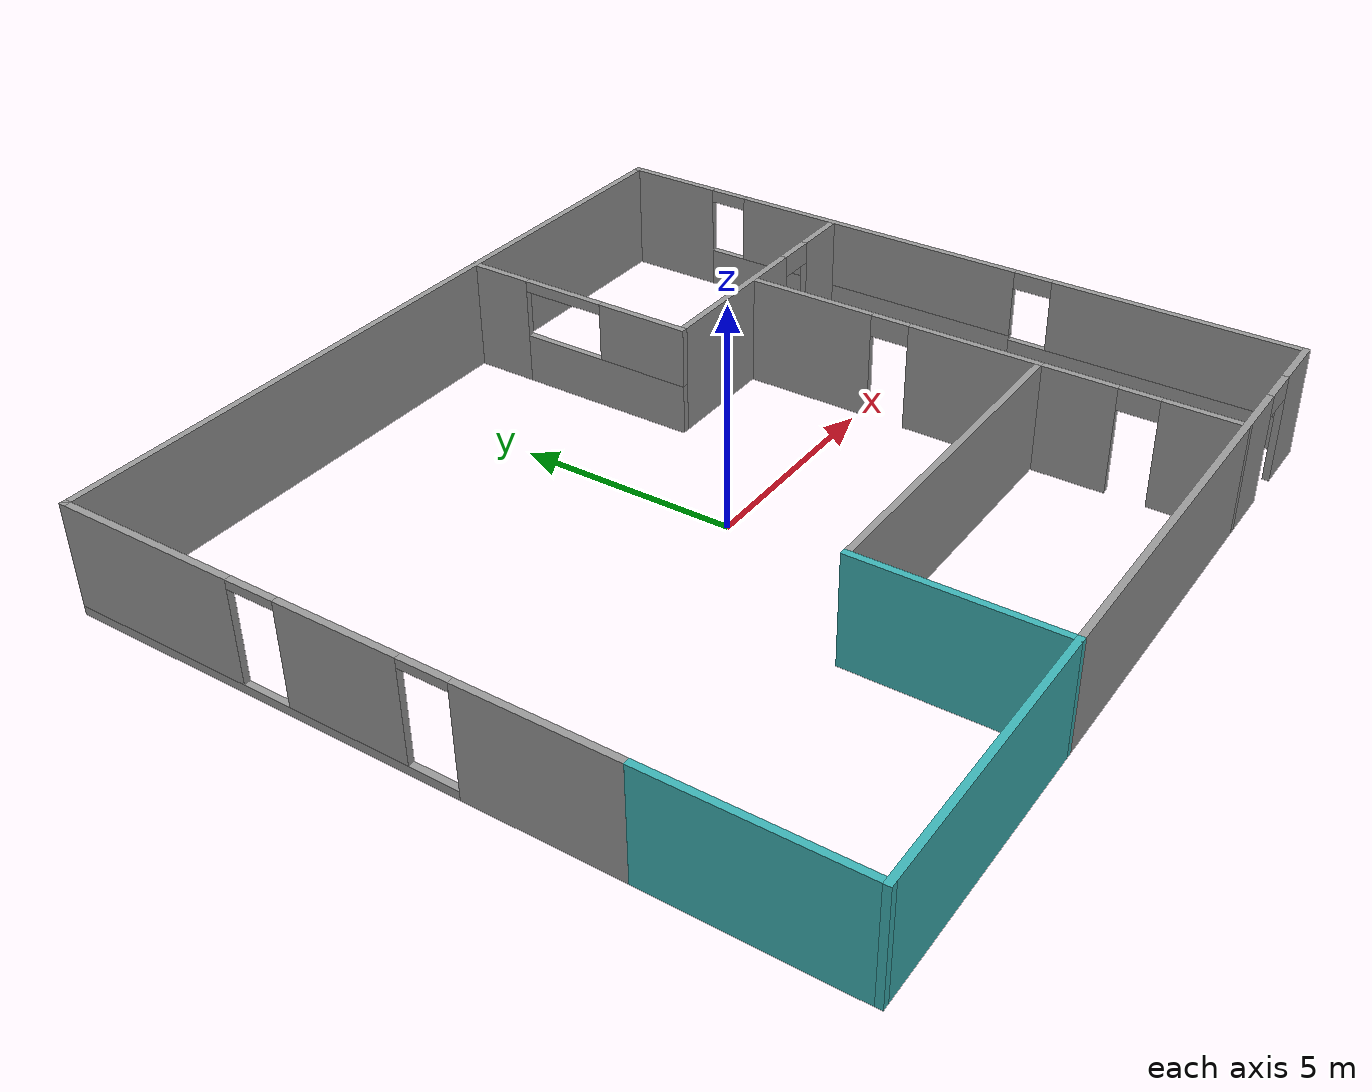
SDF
<?xml version='1.0'?>
<sdf version='1.7'>
  <model name='federicos_house_v2'>
    <link name='Wall_11'>
      <pose>8.85021 -0.00256 0 0 0 -1.5708</pose>
      <self_collide>0</self_collide>
      <enable_wind>0</enable_wind>
      <kinematic>0</kinematic>
      <visual name='Wall_11_Visual_3'>
        <pose>5.63643 0 1.65 0 -0 0</pose>
        <geometry>
          <box>
            <size>5.72713 0.15 1.7</size>
          </box>
        </geometry>
        <material>
          <script>
            <uri>file://media/materials/scripts/gazebo.material</uri>
            <name>Gazebo/Grey</name>
          </script>
          <ambient>0.952941 0.952941 0.952941 1</ambient>
          <shader type='pixel'/>
        </material>
        <meta>
          <layer>0</layer>
        </meta>
        <transparency>0</transparency>
        <cast_shadows>1</cast_shadows>
      </visual>
      <visual name='Wall_11_Visual_2'>
        <pose>5.18643 0 0.4 0 -0 0</pose>
        <geometry>
          <box>
            <size>6.62713 0.15 0.8</size>
          </box>
        </geometry>
        <material>
          <script>
            <uri>file://media/materials/scripts/gazebo.material</uri>
            <name>Gazebo/Grey</name>
          </script>
          <ambient>0.952941 0.952941 0.952941 1</ambient>
          <shader type='pixel'/>
        </material>
        <meta>
          <layer>0</layer>
        </meta>
        <transparency>0</transparency>
        <cast_shadows>1</cast_shadows>
      </visual>
      <visual name='Wall_11_Visual_6'>
        <pose>-5.72165 0 2.35 0 -0 0</pose>
        <geometry>
          <box>
            <size>0.9 0.15 0.3</size>
          </box>
        </geometry>
        <material>
          <script>
            <uri>file://media/materials/scripts/gazebo.material</uri>
            <name>Gazebo/Grey</name>
          </script>
          <ambient>0.952941 0.952941 0.952941 1</ambient>
          <shader type='pixel'/>
        </material>
        <meta>
          <layer>0</layer>
        </meta>
        <transparency>0</transparency>
        <cast_shadows>1</cast_shadows>
      </visual>
      <visual name='Wall_11_Visual_5'>
        <pose>2.32287 0 2.3 0 -0 0</pose>
        <geometry>
          <box>
            <size>0.9 0.15 0.4</size>
          </box>
        </geometry>
        <material>
          <script>
            <uri>file://media/materials/scripts/gazebo.material</uri>
            <name>Gazebo/Grey</name>
          </script>
          <ambient>0.952941 0.952941 0.952941 1</ambient>
          <shader type='pixel'/>
        </material>
        <meta>
          <layer>0</layer>
        </meta>
        <transparency>0</transparency>
        <cast_shadows>1</cast_shadows>
      </visual>
      <visual name='Wall_11_Visual_0'>
        <pose>-7.33583 0 1.25 0 -0 0</pose>
        <geometry>
          <box>
            <size>2.32835 0.15 2.5</size>
          </box>
        </geometry>
        <material>
          <script>
            <uri>file://media/materials/scripts/gazebo.material</uri>
            <name>Gazebo/Grey</name>
          </script>
          <ambient>0.952941 0.952941 0.952941 1</ambient>
          <shader type='pixel'/>
        </material>
        <meta>
          <layer>0</layer>
        </meta>
        <transparency>0</transparency>
        <cast_shadows>1</cast_shadows>
      </visual>
      <visual name='Wall_11_Visual_1'>
        <pose>-2.14939 0 0.45 0 -0 0</pose>
        <geometry>
          <box>
            <size>8.04452 0.15 0.9</size>
          </box>
        </geometry>
        <material>
          <script>
            <uri>file://media/materials/scripts/gazebo.material</uri>
            <name>Gazebo/Grey</name>
          </script>
          <ambient>0.952941 0.952941 0.952941 1</ambient>
          <shader type='pixel'/>
        </material>
        <meta>
          <layer>0</layer>
        </meta>
        <transparency>0</transparency>
        <cast_shadows>1</cast_shadows>
      </visual>
      <visual name='Wall_11_Visual_4'>
        <pose>-1.69939 0 1.7 0 -0 0</pose>
        <geometry>
          <box>
            <size>7.14452 0.15 1.6</size>
          </box>
        </geometry>
        <material>
          <script>
            <uri>file://media/materials/scripts/gazebo.material</uri>
            <name>Gazebo/Grey</name>
          </script>
          <ambient>0.952941 0.952941 0.952941 1</ambient>
          <shader type='pixel'/>
        </material>
        <meta>
          <layer>0</layer>
        </meta>
        <transparency>0</transparency>
        <cast_shadows>1</cast_shadows>
      </visual>
      <collision name='Wall_11_Collision_0'>
        <laser_retro>0</laser_retro>
        <max_contacts>10</max_contacts>
        <pose>-7.33583 0 1.25 0 -0 0</pose>
        <geometry>
          <box>
            <size>2.32835 0.15 2.5</size>
          </box>
        </geometry>
        <surface>
          <friction>
            <ode>
              <mu>1</mu>
              <mu2>1</mu2>
              <fdir1>0 0 0</fdir1>
              <slip1>0</slip1>
              <slip2>0</slip2>
            </ode>
            <torsional>
              <coefficient>1</coefficient>
              <patch_radius>0</patch_radius>
              <surface_radius>0</surface_radius>
              <use_patch_radius>1</use_patch_radius>
              <ode>
                <slip>0</slip>
              </ode>
            </torsional>
          </friction>
          <bounce>
            <restitution_coefficient>0</restitution_coefficient>
            <threshold>1e+06</threshold>
          </bounce>
          <contact>
            <collide_without_contact>0</collide_without_contact>
            <collide_without_contact_bitmask>1</collide_without_contact_bitmask>
            <collide_bitmask>1</collide_bitmask>
            <ode>
              <soft_cfm>0</soft_cfm>
              <soft_erp>0.2</soft_erp>
              <kp>1e+13</kp>
              <kd>1</kd>
              <max_vel>0.01</max_vel>
              <min_depth>0</min_depth>
            </ode>
            <bullet>
              <split_impulse>1</split_impulse>
              <split_impulse_penetration_threshold>-0.01</split_impulse_penetration_threshold>
              <soft_cfm>0</soft_cfm>
              <soft_erp>0.2</soft_erp>
              <kp>1e+13</kp>
              <kd>1</kd>
            </bullet>
          </contact>
        </surface>
      </collision>
      <collision name='Wall_11_Collision_1'>
        <laser_retro>0</laser_retro>
        <max_contacts>10</max_contacts>
        <pose>-2.14939 0 0.45 0 -0 0</pose>
        <geometry>
          <box>
            <size>8.04452 0.15 0.9</size>
          </box>
        </geometry>
        <surface>
          <friction>
            <ode>
              <mu>1</mu>
              <mu2>1</mu2>
              <fdir1>0 0 0</fdir1>
              <slip1>0</slip1>
              <slip2>0</slip2>
            </ode>
            <torsional>
              <coefficient>1</coefficient>
              <patch_radius>0</patch_radius>
              <surface_radius>0</surface_radius>
              <use_patch_radius>1</use_patch_radius>
              <ode>
                <slip>0</slip>
              </ode>
            </torsional>
          </friction>
          <bounce>
            <restitution_coefficient>0</restitution_coefficient>
            <threshold>1e+06</threshold>
          </bounce>
          <contact>
            <collide_without_contact>0</collide_without_contact>
            <collide_without_contact_bitmask>1</collide_without_contact_bitmask>
            <collide_bitmask>1</collide_bitmask>
            <ode>
              <soft_cfm>0</soft_cfm>
              <soft_erp>0.2</soft_erp>
              <kp>1e+13</kp>
              <kd>1</kd>
              <max_vel>0.01</max_vel>
              <min_depth>0</min_depth>
            </ode>
            <bullet>
              <split_impulse>1</split_impulse>
              <split_impulse_penetration_threshold>-0.01</split_impulse_penetration_threshold>
              <soft_cfm>0</soft_cfm>
              <soft_erp>0.2</soft_erp>
              <kp>1e+13</kp>
              <kd>1</kd>
            </bullet>
          </contact>
        </surface>
      </collision>
      <collision name='Wall_11_Collision_6'>
        <laser_retro>0</laser_retro>
        <max_contacts>10</max_contacts>
        <pose>-5.72165 0 2.35 0 -0 0</pose>
        <geometry>
          <box>
            <size>0.9 0.15 0.3</size>
          </box>
        </geometry>
        <surface>
          <friction>
            <ode>
              <mu>1</mu>
              <mu2>1</mu2>
              <fdir1>0 0 0</fdir1>
              <slip1>0</slip1>
              <slip2>0</slip2>
            </ode>
            <torsional>
              <coefficient>1</coefficient>
              <patch_radius>0</patch_radius>
              <surface_radius>0</surface_radius>
              <use_patch_radius>1</use_patch_radius>
              <ode>
                <slip>0</slip>
              </ode>
            </torsional>
          </friction>
          <bounce>
            <restitution_coefficient>0</restitution_coefficient>
            <threshold>1e+06</threshold>
          </bounce>
          <contact>
            <collide_without_contact>0</collide_without_contact>
            <collide_without_contact_bitmask>1</collide_without_contact_bitmask>
            <collide_bitmask>1</collide_bitmask>
            <ode>
              <soft_cfm>0</soft_cfm>
              <soft_erp>0.2</soft_erp>
              <kp>1e+13</kp>
              <kd>1</kd>
              <max_vel>0.01</max_vel>
              <min_depth>0</min_depth>
            </ode>
            <bullet>
              <split_impulse>1</split_impulse>
              <split_impulse_penetration_threshold>-0.01</split_impulse_penetration_threshold>
              <soft_cfm>0</soft_cfm>
              <soft_erp>0.2</soft_erp>
              <kp>1e+13</kp>
              <kd>1</kd>
            </bullet>
          </contact>
        </surface>
      </collision>
      <collision name='Wall_11_Collision_2'>
        <laser_retro>0</laser_retro>
        <max_contacts>10</max_contacts>
        <pose>5.18643 0 0.4 0 -0 0</pose>
        <geometry>
          <box>
            <size>6.62713 0.15 0.8</size>
          </box>
        </geometry>
        <surface>
          <friction>
            <ode>
              <mu>1</mu>
              <mu2>1</mu2>
              <fdir1>0 0 0</fdir1>
              <slip1>0</slip1>
              <slip2>0</slip2>
            </ode>
            <torsional>
              <coefficient>1</coefficient>
              <patch_radius>0</patch_radius>
              <surface_radius>0</surface_radius>
              <use_patch_radius>1</use_patch_radius>
              <ode>
                <slip>0</slip>
              </ode>
            </torsional>
          </friction>
          <bounce>
            <restitution_coefficient>0</restitution_coefficient>
            <threshold>1e+06</threshold>
          </bounce>
          <contact>
            <collide_without_contact>0</collide_without_contact>
            <collide_without_contact_bitmask>1</collide_without_contact_bitmask>
            <collide_bitmask>1</collide_bitmask>
            <ode>
              <soft_cfm>0</soft_cfm>
              <soft_erp>0.2</soft_erp>
              <kp>1e+13</kp>
              <kd>1</kd>
              <max_vel>0.01</max_vel>
              <min_depth>0</min_depth>
            </ode>
            <bullet>
              <split_impulse>1</split_impulse>
              <split_impulse_penetration_threshold>-0.01</split_impulse_penetration_threshold>
              <soft_cfm>0</soft_cfm>
              <soft_erp>0.2</soft_erp>
              <kp>1e+13</kp>
              <kd>1</kd>
            </bullet>
          </contact>
        </surface>
      </collision>
      <collision name='Wall_11_Collision_5'>
        <laser_retro>0</laser_retro>
        <max_contacts>10</max_contacts>
        <pose>2.32287 0 2.3 0 -0 0</pose>
        <geometry>
          <box>
            <size>0.9 0.15 0.4</size>
          </box>
        </geometry>
        <surface>
          <friction>
            <ode>
              <mu>1</mu>
              <mu2>1</mu2>
              <fdir1>0 0 0</fdir1>
              <slip1>0</slip1>
              <slip2>0</slip2>
            </ode>
            <torsional>
              <coefficient>1</coefficient>
              <patch_radius>0</patch_radius>
              <surface_radius>0</surface_radius>
              <use_patch_radius>1</use_patch_radius>
              <ode>
                <slip>0</slip>
              </ode>
            </torsional>
          </friction>
          <bounce>
            <restitution_coefficient>0</restitution_coefficient>
            <threshold>1e+06</threshold>
          </bounce>
          <contact>
            <collide_without_contact>0</collide_without_contact>
            <collide_without_contact_bitmask>1</collide_without_contact_bitmask>
            <collide_bitmask>1</collide_bitmask>
            <ode>
              <soft_cfm>0</soft_cfm>
              <soft_erp>0.2</soft_erp>
              <kp>1e+13</kp>
              <kd>1</kd>
              <max_vel>0.01</max_vel>
              <min_depth>0</min_depth>
            </ode>
            <bullet>
              <split_impulse>1</split_impulse>
              <split_impulse_penetration_threshold>-0.01</split_impulse_penetration_threshold>
              <soft_cfm>0</soft_cfm>
              <soft_erp>0.2</soft_erp>
              <kp>1e+13</kp>
              <kd>1</kd>
            </bullet>
          </contact>
        </surface>
      </collision>
      <collision name='Wall_11_Collision_3'>
        <laser_retro>0</laser_retro>
        <max_contacts>10</max_contacts>
        <pose>5.63643 0 1.65 0 -0 0</pose>
        <geometry>
          <box>
            <size>5.72713 0.15 1.7</size>
          </box>
        </geometry>
        <surface>
          <friction>
            <ode>
              <mu>1</mu>
              <mu2>1</mu2>
              <fdir1>0 0 0</fdir1>
              <slip1>0</slip1>
              <slip2>0</slip2>
            </ode>
            <torsional>
              <coefficient>1</coefficient>
              <patch_radius>0</patch_radius>
              <surface_radius>0</surface_radius>
              <use_patch_radius>1</use_patch_radius>
              <ode>
                <slip>0</slip>
              </ode>
            </torsional>
          </friction>
          <bounce>
            <restitution_coefficient>0</restitution_coefficient>
            <threshold>1e+06</threshold>
          </bounce>
          <contact>
            <collide_without_contact>0</collide_without_contact>
            <collide_without_contact_bitmask>1</collide_without_contact_bitmask>
            <collide_bitmask>1</collide_bitmask>
            <ode>
              <soft_cfm>0</soft_cfm>
              <soft_erp>0.2</soft_erp>
              <kp>1e+13</kp>
              <kd>1</kd>
              <max_vel>0.01</max_vel>
              <min_depth>0</min_depth>
            </ode>
            <bullet>
              <split_impulse>1</split_impulse>
              <split_impulse_penetration_threshold>-0.01</split_impulse_penetration_threshold>
              <soft_cfm>0</soft_cfm>
              <soft_erp>0.2</soft_erp>
              <kp>1e+13</kp>
              <kd>1</kd>
            </bullet>
          </contact>
        </surface>
      </collision>
      <collision name='Wall_11_Collision_4'>
        <laser_retro>0</laser_retro>
        <max_contacts>10</max_contacts>
        <pose>-1.69939 0 1.7 0 -0 0</pose>
        <geometry>
          <box>
            <size>7.14452 0.15 1.6</size>
          </box>
        </geometry>
        <surface>
          <friction>
            <ode>
              <mu>1</mu>
              <mu2>1</mu2>
              <fdir1>0 0 0</fdir1>
              <slip1>0</slip1>
              <slip2>0</slip2>
            </ode>
            <torsional>
              <coefficient>1</coefficient>
              <patch_radius>0</patch_radius>
              <surface_radius>0</surface_radius>
              <use_patch_radius>1</use_patch_radius>
              <ode>
                <slip>0</slip>
              </ode>
            </torsional>
          </friction>
          <bounce>
            <restitution_coefficient>0</restitution_coefficient>
            <threshold>1e+06</threshold>
          </bounce>
          <contact>
            <collide_without_contact>0</collide_without_contact>
            <collide_without_contact_bitmask>1</collide_without_contact_bitmask>
            <collide_bitmask>1</collide_bitmask>
            <ode>
              <soft_cfm>0</soft_cfm>
              <soft_erp>0.2</soft_erp>
              <kp>1e+13</kp>
              <kd>1</kd>
              <max_vel>0.01</max_vel>
              <min_depth>0</min_depth>
            </ode>
            <bullet>
              <split_impulse>1</split_impulse>
              <split_impulse_penetration_threshold>-0.01</split_impulse_penetration_threshold>
              <soft_cfm>0</soft_cfm>
              <soft_erp>0.2</soft_erp>
              <kp>1e+13</kp>
              <kd>1</kd>
            </bullet>
          </contact>
        </surface>
      </collision>
    </link>
    <link name='Wall_12'>
      <pose>3.17521 -8.42756 0 0 -0 3.14159</pose>
      <self_collide>0</self_collide>
      <enable_wind>0</enable_wind>
      <kinematic>0</kinematic>
      <gravity>1</gravity>
      <inertial>
        <mass>1</mass>
        <pose>0 0 0 0 -0 0</pose>
        <inertia>
          <ixx>1</ixx>
          <ixy>0</ixy>
          <ixz>0</ixz>
          <iyy>1</iyy>
          <iyz>0</iyz>
          <izz>1</izz>
        </inertia>
      </inertial>
      <visual name='Wall_12_Visual_2'>
        <pose>-3.94881 0 2.25 0 -0 0</pose>
        <geometry>
          <box>
            <size>0.9 0.15 0.5</size>
          </box>
        </geometry>
        <material>
          <script>
            <uri>file://media/materials/scripts/gazebo.material</uri>
            <name>Gazebo/Grey</name>
          </script>
          <ambient>0.953 0.953 0.953 1</ambient>
          <shader type='pixel'>
            <normal_map>__default__</normal_map>
          </shader>
          <diffuse>0.7 0.7 0.7 1</diffuse>
          <specular>0.01 0.01 0.01 1</specular>
          <emissive>0 0 0 1</emissive>
        </material>
        <meta>
          <layer>0</layer>
        </meta>
        <transparency>0</transparency>
        <cast_shadows>1</cast_shadows>
      </visual>
      <visual name='Wall_12_Visual_1'>
        <pose>1.05 0 1.25 0 -0 0</pose>
        <geometry>
          <box>
            <size>9.1 0.15 2.5</size>
          </box>
        </geometry>
        <material>
          <script>
            <uri>file://media/materials/scripts/gazebo.material</uri>
            <name>Gazebo/Grey</name>
          </script>
          <ambient>0.953 0.953 0.953 1</ambient>
          <shader type='pixel'>
            <normal_map>__default__</normal_map>
          </shader>
          <diffuse>0.7 0.7 0.7 1</diffuse>
          <specular>0.01 0.01 0.01 1</specular>
          <emissive>0 0 0 1</emissive>
        </material>
        <meta>
          <layer>0</layer>
        </meta>
        <transparency>0</transparency>
        <cast_shadows>1</cast_shadows>
      </visual>
      <visual name='Wall_12_Visual_0'>
        <pose>-5.0744 0 1.25 0 -0 0</pose>
        <geometry>
          <box>
            <size>1.35119 0.15 2.5</size>
          </box>
        </geometry>
        <material>
          <script>
            <uri>file://media/materials/scripts/gazebo.material</uri>
            <name>Gazebo/Grey</name>
          </script>
          <ambient>0.953 0.953 0.953 1</ambient>
          <shader type='pixel'>
            <normal_map>__default__</normal_map>
          </shader>
          <diffuse>0.7 0.7 0.7 1</diffuse>
          <specular>0.01 0.01 0.01 1</specular>
          <emissive>0 0 0 1</emissive>
        </material>
        <meta>
          <layer>0</layer>
        </meta>
        <transparency>0</transparency>
        <cast_shadows>1</cast_shadows>
      </visual>
      <collision name='Wall_12_Collision_1'>
        <laser_retro>0</laser_retro>
        <max_contacts>10</max_contacts>
        <pose>1.05 0 1.25 0 -0 0</pose>
        <geometry>
          <box>
            <size>9.1 0.15 2.5</size>
          </box>
        </geometry>
        <surface>
          <friction>
            <ode>
              <mu>1</mu>
              <mu2>1</mu2>
              <fdir1>0 0 0</fdir1>
              <slip1>0</slip1>
              <slip2>0</slip2>
            </ode>
            <torsional>
              <coefficient>1</coefficient>
              <patch_radius>0</patch_radius>
              <surface_radius>0</surface_radius>
              <use_patch_radius>1</use_patch_radius>
              <ode>
                <slip>0</slip>
              </ode>
            </torsional>
          </friction>
          <bounce>
            <restitution_coefficient>0</restitution_coefficient>
            <threshold>1e+06</threshold>
          </bounce>
          <contact>
            <collide_without_contact>0</collide_without_contact>
            <collide_without_contact_bitmask>1</collide_without_contact_bitmask>
            <collide_bitmask>1</collide_bitmask>
            <ode>
              <soft_cfm>0</soft_cfm>
              <soft_erp>0.2</soft_erp>
              <kp>1e+13</kp>
              <kd>1</kd>
              <max_vel>0.01</max_vel>
              <min_depth>0</min_depth>
            </ode>
            <bullet>
              <split_impulse>1</split_impulse>
              <split_impulse_penetration_threshold>-0.01</split_impulse_penetration_threshold>
              <soft_cfm>0</soft_cfm>
              <soft_erp>0.2</soft_erp>
              <kp>1e+13</kp>
              <kd>1</kd>
            </bullet>
          </contact>
        </surface>
      </collision>
      <collision name='Wall_12_Collision_0'>
        <laser_retro>0</laser_retro>
        <max_contacts>10</max_contacts>
        <pose>-5.0744 0 1.25 0 -0 0</pose>
        <geometry>
          <box>
            <size>1.35119 0.15 2.5</size>
          </box>
        </geometry>
        <surface>
          <friction>
            <ode>
              <mu>1</mu>
              <mu2>1</mu2>
              <fdir1>0 0 0</fdir1>
              <slip1>0</slip1>
              <slip2>0</slip2>
            </ode>
            <torsional>
              <coefficient>1</coefficient>
              <patch_radius>0</patch_radius>
              <surface_radius>0</surface_radius>
              <use_patch_radius>1</use_patch_radius>
              <ode>
                <slip>0</slip>
              </ode>
            </torsional>
          </friction>
          <bounce>
            <restitution_coefficient>0</restitution_coefficient>
            <threshold>1e+06</threshold>
          </bounce>
          <contact>
            <collide_without_contact>0</collide_without_contact>
            <collide_without_contact_bitmask>1</collide_without_contact_bitmask>
            <collide_bitmask>1</collide_bitmask>
            <ode>
              <soft_cfm>0</soft_cfm>
              <soft_erp>0.2</soft_erp>
              <kp>1e+13</kp>
              <kd>1</kd>
              <max_vel>0.01</max_vel>
              <min_depth>0</min_depth>
            </ode>
            <bullet>
              <split_impulse>1</split_impulse>
              <split_impulse_penetration_threshold>-0.01</split_impulse_penetration_threshold>
              <soft_cfm>0</soft_cfm>
              <soft_erp>0.2</soft_erp>
              <kp>1e+13</kp>
              <kd>1</kd>
            </bullet>
          </contact>
        </surface>
      </collision>
      <collision name='Wall_12_Collision_2'>
        <laser_retro>0</laser_retro>
        <max_contacts>10</max_contacts>
        <pose>-3.94881 0 2.25 0 -0 0</pose>
        <geometry>
          <box>
            <size>0.9 0.15 0.5</size>
          </box>
        </geometry>
        <surface>
          <friction>
            <ode>
              <mu>1</mu>
              <mu2>1</mu2>
              <fdir1>0 0 0</fdir1>
              <slip1>0</slip1>
              <slip2>0</slip2>
            </ode>
            <torsional>
              <coefficient>1</coefficient>
              <patch_radius>0</patch_radius>
              <surface_radius>0</surface_radius>
              <use_patch_radius>1</use_patch_radius>
              <ode>
                <slip>0</slip>
              </ode>
            </torsional>
          </friction>
          <bounce>
            <restitution_coefficient>0</restitution_coefficient>
            <threshold>1e+06</threshold>
          </bounce>
          <contact>
            <collide_without_contact>0</collide_without_contact>
            <collide_without_contact_bitmask>1</collide_without_contact_bitmask>
            <collide_bitmask>1</collide_bitmask>
            <ode>
              <soft_cfm>0</soft_cfm>
              <soft_erp>0.2</soft_erp>
              <kp>1e+13</kp>
              <kd>1</kd>
              <max_vel>0.01</max_vel>
              <min_depth>0</min_depth>
            </ode>
            <bullet>
              <split_impulse>1</split_impulse>
              <split_impulse_penetration_threshold>-0.01</split_impulse_penetration_threshold>
              <soft_cfm>0</soft_cfm>
              <soft_erp>0.2</soft_erp>
              <kp>1e+13</kp>
              <kd>1</kd>
            </bullet>
          </contact>
        </surface>
      </collision>
    </link>
    <link name='Wall_13'>
      <pose>-5.67479 -8.42756 0 0 -0 3.14159</pose>
      <self_collide>0</self_collide>
      <enable_wind>0</enable_wind>
      <kinematic>0</kinematic>
      <visual name='Wall_13_Visual'>
        <pose>0 0 1.25 0 -0 0</pose>
        <geometry>
          <box>
            <size>6.5 0.15 2.5</size>
          </box>
        </geometry>
        <material>
          <script>
            <uri>file://media/materials/scripts/gazebo.material</uri>
            <name>Gazebo/Grey</name>
          </script>
          <ambient>0.239216 0.705882 0.713726 1</ambient>
          <shader type='pixel'/>
        </material>
        <meta>
          <layer>0</layer>
        </meta>
        <transparency>0</transparency>
        <cast_shadows>1</cast_shadows>
      </visual>
      <collision name='Wall_13_Collision'>
        <laser_retro>0</laser_retro>
        <max_contacts>10</max_contacts>
        <pose>0 0 1.25 0 -0 0</pose>
        <geometry>
          <box>
            <size>6.5 0.15 2.5</size>
          </box>
        </geometry>
        <surface>
          <friction>
            <ode>
              <mu>1</mu>
              <mu2>1</mu2>
              <fdir1>0 0 0</fdir1>
              <slip1>0</slip1>
              <slip2>0</slip2>
            </ode>
            <torsional>
              <coefficient>1</coefficient>
              <patch_radius>0</patch_radius>
              <surface_radius>0</surface_radius>
              <use_patch_radius>1</use_patch_radius>
              <ode>
                <slip>0</slip>
              </ode>
            </torsional>
          </friction>
          <bounce>
            <restitution_coefficient>0</restitution_coefficient>
            <threshold>1e+06</threshold>
          </bounce>
          <contact>
            <collide_without_contact>0</collide_without_contact>
            <collide_without_contact_bitmask>1</collide_without_contact_bitmask>
            <collide_bitmask>1</collide_bitmask>
            <ode>
              <soft_cfm>0</soft_cfm>
              <soft_erp>0.2</soft_erp>
              <kp>1e+13</kp>
              <kd>1</kd>
              <max_vel>0.01</max_vel>
              <min_depth>0</min_depth>
            </ode>
            <bullet>
              <split_impulse>1</split_impulse>
              <split_impulse_penetration_threshold>-0.01</split_impulse_penetration_threshold>
              <soft_cfm>0</soft_cfm>
              <soft_erp>0.2</soft_erp>
              <kp>1e+13</kp>
              <kd>1</kd>
            </bullet>
          </contact>
        </surface>
      </collision>
    </link>
    <link name='Wall_18'>
      <pose>-8.84979 -6.25256 0 0 -0 1.5708</pose>
      <self_collide>0</self_collide>
      <enable_wind>0</enable_wind>
      <kinematic>0</kinematic>
      <visual name='Wall_18_Visual'>
        <pose>0 0 1.25 0 -0 0</pose>
        <geometry>
          <box>
            <size>4.5 0.15 2.5</size>
          </box>
        </geometry>
        <material>
          <script>
            <uri>file://media/materials/scripts/gazebo.material</uri>
            <name>Gazebo/Grey</name>
          </script>
          <ambient>0.239216 0.705882 0.713726 1</ambient>
          <shader type='pixel'/>
        </material>
        <meta>
          <layer>0</layer>
        </meta>
        <transparency>0</transparency>
        <cast_shadows>1</cast_shadows>
      </visual>
      <collision name='Wall_18_Collision'>
        <laser_retro>0</laser_retro>
        <max_contacts>10</max_contacts>
        <pose>0 0 1.25 0 -0 0</pose>
        <geometry>
          <box>
            <size>4.5 0.15 2.5</size>
          </box>
        </geometry>
        <surface>
          <friction>
            <ode>
              <mu>1</mu>
              <mu2>1</mu2>
              <fdir1>0 0 0</fdir1>
              <slip1>0</slip1>
              <slip2>0</slip2>
            </ode>
            <torsional>
              <coefficient>1</coefficient>
              <patch_radius>0</patch_radius>
              <surface_radius>0</surface_radius>
              <use_patch_radius>1</use_patch_radius>
              <ode>
                <slip>0</slip>
              </ode>
            </torsional>
          </friction>
          <bounce>
            <restitution_coefficient>0</restitution_coefficient>
            <threshold>1e+06</threshold>
          </bounce>
          <contact>
            <collide_without_contact>0</collide_without_contact>
            <collide_without_contact_bitmask>1</collide_without_contact_bitmask>
            <collide_bitmask>1</collide_bitmask>
            <ode>
              <soft_cfm>0</soft_cfm>
              <soft_erp>0.2</soft_erp>
              <kp>1e+13</kp>
              <kd>1</kd>
              <max_vel>0.01</max_vel>
              <min_depth>0</min_depth>
            </ode>
            <bullet>
              <split_impulse>1</split_impulse>
              <split_impulse_penetration_threshold>-0.01</split_impulse_penetration_threshold>
              <soft_cfm>0</soft_cfm>
              <soft_erp>0.2</soft_erp>
              <kp>1e+13</kp>
              <kd>1</kd>
            </bullet>
          </contact>
        </surface>
      </collision>
    </link>
    <link name='Wall_19'>
      <pose>-8.85 2.17222 0 0 -0 1.57083</pose>
      <self_collide>0</self_collide>
      <enable_wind>0</enable_wind>
      <kinematic>0</kinematic>
      <gravity>1</gravity>
      <inertial>
        <mass>1</mass>
        <pose>0 0 0 0 -0 0</pose>
        <inertia>
          <ixx>1</ixx>
          <ixy>0</ixy>
          <ixz>0</ixz>
          <iyy>1</iyy>
          <iyz>0</iyz>
          <izz>1</izz>
        </inertia>
      </inertial>
      <visual name='Wall_19_Visual_4'>
        <pose>-2.22799 0 2.4 0 -0 0</pose>
        <geometry>
          <box>
            <size>1.1 0.15 0.2</size>
          </box>
        </geometry>
        <material>
          <script>
            <uri>file://media/materials/scripts/gazebo.material</uri>
            <name>Gazebo/Grey</name>
          </script>
          <ambient>0.953 0.953 0.953 1</ambient>
          <shader type='pixel'>
            <normal_map>__default__</normal_map>
          </shader>
          <diffuse>0.7 0.7 0.7 1</diffuse>
          <specular>0.01 0.01 0.01 1</specular>
          <emissive>0 0 0 1</emissive>
        </material>
        <meta>
          <layer>0</layer>
        </meta>
        <transparency>0</transparency>
        <cast_shadows>1</cast_shadows>
      </visual>
      <visual name='Wall_19_Visual_2'>
        <pose>-0.320942 0 1.35 0 -0 0</pose>
        <geometry>
          <box>
            <size>2.71409 0.15 2.3</size>
          </box>
        </geometry>
        <material>
          <script>
            <uri>file://media/materials/scripts/gazebo.material</uri>
            <name>Gazebo/Grey</name>
          </script>
          <ambient>0.953 0.953 0.953 1</ambient>
          <shader type='pixel'>
            <normal_map>__default__</normal_map>
          </shader>
          <diffuse>0.7 0.7 0.7 1</diffuse>
          <specular>0.01 0.01 0.01 1</specular>
          <emissive>0 0 0 1</emissive>
        </material>
        <meta>
          <layer>0</layer>
        </meta>
        <transparency>0</transparency>
        <cast_shadows>1</cast_shadows>
      </visual>
      <visual name='Wall_19_Visual_1'>
        <pose>1.7734 0 0.1 0 -0 0</pose>
        <geometry>
          <box>
            <size>9.10277 0.15 0.2</size>
          </box>
        </geometry>
        <material>
          <script>
            <uri>file://media/materials/scripts/gazebo.material</uri>
            <name>Gazebo/Grey</name>
          </script>
          <ambient>0.953 0.953 0.953 1</ambient>
          <shader type='pixel'>
            <normal_map>__default__</normal_map>
          </shader>
          <diffuse>0.7 0.7 0.7 1</diffuse>
          <specular>0.01 0.01 0.01 1</specular>
          <emissive>0 0 0 1</emissive>
        </material>
        <meta>
          <layer>0</layer>
        </meta>
        <transparency>0</transparency>
        <cast_shadows>1</cast_shadows>
      </visual>
      <visual name='Wall_19_Visual'>
        <pose>-4.47478 0 1.25 0 -0 0</pose>
        <geometry>
          <box>
            <size>3.3979 0.15 2.5</size>
          </box>
        </geometry>
        <material>
          <script>
            <uri>file://media/materials/scripts/gazebo.material</uri>
            <name>Gazebo/Grey</name>
          </script>
          <ambient>0.953 0.953 0.953 1</ambient>
          <shader type='pixel'>
            <normal_map>__default__</normal_map>
          </shader>
          <diffuse>0.7 0.7 0.7 1</diffuse>
          <specular>0.01 0.01 0.01 1</specular>
          <emissive>0 0 0 1</emissive>
        </material>
        <meta>
          <layer>0</layer>
        </meta>
        <transparency>0</transparency>
        <cast_shadows>1</cast_shadows>
      </visual>
      <visual name='Wall_19_Visual_3'>
        <pose>4.23044 0 1.35 0 -0 0</pose>
        <geometry>
          <box>
            <size>4.18867 0.15 2.3</size>
          </box>
        </geometry>
        <material>
          <script>
            <uri>file://media/materials/scripts/gazebo.material</uri>
            <name>Gazebo/Grey</name>
          </script>
          <ambient>0.953 0.953 0.953 1</ambient>
          <shader type='pixel'>
            <normal_map>__default__</normal_map>
          </shader>
          <diffuse>0.7 0.7 0.7 1</diffuse>
          <specular>0.01 0.01 0.01 1</specular>
          <emissive>0 0 0 1</emissive>
        </material>
        <meta>
          <layer>0</layer>
        </meta>
        <transparency>0</transparency>
        <cast_shadows>1</cast_shadows>
      </visual>
      <visual name='Wall_19_Visual_5'>
        <pose>1.58611 0 2.4 0 -0 0</pose>
        <geometry>
          <box>
            <size>1.1 0.15 0.2</size>
          </box>
        </geometry>
        <material>
          <script>
            <uri>file://media/materials/scripts/gazebo.material</uri>
            <name>Gazebo/Grey</name>
          </script>
          <ambient>0.953 0.953 0.953 1</ambient>
          <shader type='pixel'>
            <normal_map>__default__</normal_map>
          </shader>
          <diffuse>0.7 0.7 0.7 1</diffuse>
          <specular>0.01 0.01 0.01 1</specular>
          <emissive>0 0 0 1</emissive>
        </material>
        <meta>
          <layer>0</layer>
        </meta>
        <transparency>0</transparency>
        <cast_shadows>1</cast_shadows>
      </visual>
      <collision name='Wall_19_Collision_1'>
        <laser_retro>0</laser_retro>
        <max_contacts>10</max_contacts>
        <pose>1.7734 0 0.1 0 -0 0</pose>
        <geometry>
          <box>
            <size>9.10277 0.15 0.2</size>
          </box>
        </geometry>
        <surface>
          <friction>
            <ode>
              <mu>1</mu>
              <mu2>1</mu2>
              <fdir1>0 0 0</fdir1>
              <slip1>0</slip1>
              <slip2>0</slip2>
            </ode>
            <torsional>
              <coefficient>1</coefficient>
              <patch_radius>0</patch_radius>
              <surface_radius>0</surface_radius>
              <use_patch_radius>1</use_patch_radius>
              <ode>
                <slip>0</slip>
              </ode>
            </torsional>
          </friction>
          <bounce>
            <restitution_coefficient>0</restitution_coefficient>
            <threshold>1e+06</threshold>
          </bounce>
          <contact>
            <collide_without_contact>0</collide_without_contact>
            <collide_without_contact_bitmask>1</collide_without_contact_bitmask>
            <collide_bitmask>1</collide_bitmask>
            <ode>
              <soft_cfm>0</soft_cfm>
              <soft_erp>0.2</soft_erp>
              <kp>1e+13</kp>
              <kd>1</kd>
              <max_vel>0.01</max_vel>
              <min_depth>0</min_depth>
            </ode>
            <bullet>
              <split_impulse>1</split_impulse>
              <split_impulse_penetration_threshold>-0.01</split_impulse_penetration_threshold>
              <soft_cfm>0</soft_cfm>
              <soft_erp>0.2</soft_erp>
              <kp>1e+13</kp>
              <kd>1</kd>
            </bullet>
          </contact>
        </surface>
      </collision>
      <collision name='Wall_19_Collision_4'>
        <laser_retro>0</laser_retro>
        <max_contacts>10</max_contacts>
        <pose>-2.22799 0 2.4 0 -0 0</pose>
        <geometry>
          <box>
            <size>1.1 0.15 0.2</size>
          </box>
        </geometry>
        <surface>
          <friction>
            <ode>
              <mu>1</mu>
              <mu2>1</mu2>
              <fdir1>0 0 0</fdir1>
              <slip1>0</slip1>
              <slip2>0</slip2>
            </ode>
            <torsional>
              <coefficient>1</coefficient>
              <patch_radius>0</patch_radius>
              <surface_radius>0</surface_radius>
              <use_patch_radius>1</use_patch_radius>
              <ode>
                <slip>0</slip>
              </ode>
            </torsional>
          </friction>
          <bounce>
            <restitution_coefficient>0</restitution_coefficient>
            <threshold>1e+06</threshold>
          </bounce>
          <contact>
            <collide_without_contact>0</collide_without_contact>
            <collide_without_contact_bitmask>1</collide_without_contact_bitmask>
            <collide_bitmask>1</collide_bitmask>
            <ode>
              <soft_cfm>0</soft_cfm>
              <soft_erp>0.2</soft_erp>
              <kp>1e+13</kp>
              <kd>1</kd>
              <max_vel>0.01</max_vel>
              <min_depth>0</min_depth>
            </ode>
            <bullet>
              <split_impulse>1</split_impulse>
              <split_impulse_penetration_threshold>-0.01</split_impulse_penetration_threshold>
              <soft_cfm>0</soft_cfm>
              <soft_erp>0.2</soft_erp>
              <kp>1e+13</kp>
              <kd>1</kd>
            </bullet>
          </contact>
        </surface>
      </collision>
      <collision name='Wall_19_Collision_5'>
        <laser_retro>0</laser_retro>
        <max_contacts>10</max_contacts>
        <pose>1.58611 0 2.4 0 -0 0</pose>
        <geometry>
          <box>
            <size>1.1 0.15 0.2</size>
          </box>
        </geometry>
        <surface>
          <friction>
            <ode>
              <mu>1</mu>
              <mu2>1</mu2>
              <fdir1>0 0 0</fdir1>
              <slip1>0</slip1>
              <slip2>0</slip2>
            </ode>
            <torsional>
              <coefficient>1</coefficient>
              <patch_radius>0</patch_radius>
              <surface_radius>0</surface_radius>
              <use_patch_radius>1</use_patch_radius>
              <ode>
                <slip>0</slip>
              </ode>
            </torsional>
          </friction>
          <bounce>
            <restitution_coefficient>0</restitution_coefficient>
            <threshold>1e+06</threshold>
          </bounce>
          <contact>
            <collide_without_contact>0</collide_without_contact>
            <collide_without_contact_bitmask>1</collide_without_contact_bitmask>
            <collide_bitmask>1</collide_bitmask>
            <ode>
              <soft_cfm>0</soft_cfm>
              <soft_erp>0.2</soft_erp>
              <kp>1e+13</kp>
              <kd>1</kd>
              <max_vel>0.01</max_vel>
              <min_depth>0</min_depth>
            </ode>
            <bullet>
              <split_impulse>1</split_impulse>
              <split_impulse_penetration_threshold>-0.01</split_impulse_penetration_threshold>
              <soft_cfm>0</soft_cfm>
              <soft_erp>0.2</soft_erp>
              <kp>1e+13</kp>
              <kd>1</kd>
            </bullet>
          </contact>
        </surface>
      </collision>
      <collision name='Wall_19_Collision'>
        <laser_retro>0</laser_retro>
        <max_contacts>10</max_contacts>
        <pose>-4.47478 0 1.25 0 -0 0</pose>
        <geometry>
          <box>
            <size>3.39679 0.15 2.5</size>
          </box>
        </geometry>
        <surface>
          <friction>
            <ode>
              <mu>1</mu>
              <mu2>1</mu2>
              <fdir1>0 0 0</fdir1>
              <slip1>0</slip1>
              <slip2>0</slip2>
            </ode>
            <torsional>
              <coefficient>1</coefficient>
              <patch_radius>0</patch_radius>
              <surface_radius>0</surface_radius>
              <use_patch_radius>1</use_patch_radius>
              <ode>
                <slip>0</slip>
              </ode>
            </torsional>
          </friction>
          <bounce>
            <restitution_coefficient>0</restitution_coefficient>
            <threshold>1e+06</threshold>
          </bounce>
          <contact>
            <collide_without_contact>0</collide_without_contact>
            <collide_without_contact_bitmask>1</collide_without_contact_bitmask>
            <collide_bitmask>1</collide_bitmask>
            <ode>
              <soft_cfm>0</soft_cfm>
              <soft_erp>0.2</soft_erp>
              <kp>1e+13</kp>
              <kd>1</kd>
              <max_vel>0.01</max_vel>
              <min_depth>0</min_depth>
            </ode>
            <bullet>
              <split_impulse>1</split_impulse>
              <split_impulse_penetration_threshold>-0.01</split_impulse_penetration_threshold>
              <soft_cfm>0</soft_cfm>
              <soft_erp>0.2</soft_erp>
              <kp>1e+13</kp>
              <kd>1</kd>
            </bullet>
          </contact>
        </surface>
      </collision>
      <collision name='Wall_19_Collision_2'>
        <laser_retro>0</laser_retro>
        <max_contacts>10</max_contacts>
        <pose>-0.320942 0 1.35 0 -0 0</pose>
        <geometry>
          <box>
            <size>2.71409 0.15 2.3</size>
          </box>
        </geometry>
        <surface>
          <friction>
            <ode>
              <mu>1</mu>
              <mu2>1</mu2>
              <fdir1>0 0 0</fdir1>
              <slip1>0</slip1>
              <slip2>0</slip2>
            </ode>
            <torsional>
              <coefficient>1</coefficient>
              <patch_radius>0</patch_radius>
              <surface_radius>0</surface_radius>
              <use_patch_radius>1</use_patch_radius>
              <ode>
                <slip>0</slip>
              </ode>
            </torsional>
          </friction>
          <bounce>
            <restitution_coefficient>0</restitution_coefficient>
            <threshold>1e+06</threshold>
          </bounce>
          <contact>
            <collide_without_contact>0</collide_without_contact>
            <collide_without_contact_bitmask>1</collide_without_contact_bitmask>
            <collide_bitmask>1</collide_bitmask>
            <ode>
              <soft_cfm>0</soft_cfm>
              <soft_erp>0.2</soft_erp>
              <kp>1e+13</kp>
              <kd>1</kd>
              <max_vel>0.01</max_vel>
              <min_depth>0</min_depth>
            </ode>
            <bullet>
              <split_impulse>1</split_impulse>
              <split_impulse_penetration_threshold>-0.01</split_impulse_penetration_threshold>
              <soft_cfm>0</soft_cfm>
              <soft_erp>0.2</soft_erp>
              <kp>1e+13</kp>
              <kd>1</kd>
            </bullet>
          </contact>
        </surface>
      </collision>
      <collision name='Wall_19_Collision_3'>
        <laser_retro>0</laser_retro>
        <max_contacts>10</max_contacts>
        <pose>4.23044 0 1.35 0 -0 0</pose>
        <geometry>
          <box>
            <size>4.18867 0.15 2.3</size>
          </box>
        </geometry>
        <surface>
          <friction>
            <ode>
              <mu>1</mu>
              <mu2>1</mu2>
              <fdir1>0 0 0</fdir1>
              <slip1>0</slip1>
              <slip2>0</slip2>
            </ode>
            <torsional>
              <coefficient>1</coefficient>
              <patch_radius>0</patch_radius>
              <surface_radius>0</surface_radius>
              <use_patch_radius>1</use_patch_radius>
              <ode>
                <slip>0</slip>
              </ode>
            </torsional>
          </friction>
          <bounce>
            <restitution_coefficient>0</restitution_coefficient>
            <threshold>1e+06</threshold>
          </bounce>
          <contact>
            <collide_without_contact>0</collide_without_contact>
            <collide_without_contact_bitmask>1</collide_without_contact_bitmask>
            <collide_bitmask>1</collide_bitmask>
            <ode>
              <soft_cfm>0</soft_cfm>
              <soft_erp>0.2</soft_erp>
              <kp>1e+13</kp>
              <kd>1</kd>
              <max_vel>0.01</max_vel>
              <min_depth>0</min_depth>
            </ode>
            <bullet>
              <split_impulse>1</split_impulse>
              <split_impulse_penetration_threshold>-0.01</split_impulse_penetration_threshold>
              <soft_cfm>0</soft_cfm>
              <soft_erp>0.2</soft_erp>
              <kp>1e+13</kp>
              <kd>1</kd>
            </bullet>
          </contact>
        </surface>
      </collision>
    </link>
    <link name='Wall_20'>
      <pose>-0.000205 8.422 0 0 -0 0</pose>
      <self_collide>0</self_collide>
      <enable_wind>0</enable_wind>
      <kinematic>0</kinematic>
      <visual name='Wall_20_Visual'>
        <pose>0 0 1.25 0 -0 0</pose>
        <geometry>
          <box>
            <size>17.85 0.15 2.5</size>
          </box>
        </geometry>
        <material>
          <script>
            <uri>file://media/materials/scripts/gazebo.material</uri>
            <name>Gazebo/Grey</name>
          </script>
          <ambient>0.952941 0.952941 0.952941 1</ambient>
          <shader type='pixel'/>
        </material>
        <meta>
          <layer>0</layer>
        </meta>
        <transparency>0</transparency>
        <cast_shadows>1</cast_shadows>
      </visual>
      <collision name='Wall_20_Collision'>
        <laser_retro>0</laser_retro>
        <max_contacts>10</max_contacts>
        <pose>0 0 1.25 0 -0 0</pose>
        <geometry>
          <box>
            <size>17.85 0.15 2.5</size>
          </box>
        </geometry>
        <surface>
          <friction>
            <ode>
              <mu>1</mu>
              <mu2>1</mu2>
              <fdir1>0 0 0</fdir1>
              <slip1>0</slip1>
              <slip2>0</slip2>
            </ode>
            <torsional>
              <coefficient>1</coefficient>
              <patch_radius>0</patch_radius>
              <surface_radius>0</surface_radius>
              <use_patch_radius>1</use_patch_radius>
              <ode>
                <slip>0</slip>
              </ode>
            </torsional>
          </friction>
          <bounce>
            <restitution_coefficient>0</restitution_coefficient>
            <threshold>1e+06</threshold>
          </bounce>
          <contact>
            <collide_without_contact>0</collide_without_contact>
            <collide_without_contact_bitmask>1</collide_without_contact_bitmask>
            <collide_bitmask>1</collide_bitmask>
            <ode>
              <soft_cfm>0</soft_cfm>
              <soft_erp>0.2</soft_erp>
              <kp>1e+13</kp>
              <kd>1</kd>
              <max_vel>0.01</max_vel>
              <min_depth>0</min_depth>
            </ode>
            <bullet>
              <split_impulse>1</split_impulse>
              <split_impulse_penetration_threshold>-0.01</split_impulse_penetration_threshold>
              <soft_cfm>0</soft_cfm>
              <soft_erp>0.2</soft_erp>
              <kp>1e+13</kp>
              <kd>1</kd>
            </bullet>
          </contact>
        </surface>
      </collision>
    </link>
    <link name='Wall_22'>
      <pose>-2.5 -6.25278 0 0 -0 1.57089</pose>
      <self_collide>0</self_collide>
      <enable_wind>0</enable_wind>
      <kinematic>0</kinematic>
      <visual name='Wall_22_Visual'>
        <pose>0 0 1.25 0 -0 0</pose>
        <geometry>
          <box>
            <size>4.5 0.15 2.5</size>
          </box>
        </geometry>
        <material>
          <script>
            <uri>file://media/materials/scripts/gazebo.material</uri>
            <name>Gazebo/Grey</name>
          </script>
          <ambient>0.239216 0.705882 0.713726 1</ambient>
          <shader type='pixel'/>
        </material>
        <meta>
          <layer>0</layer>
        </meta>
        <transparency>0</transparency>
        <cast_shadows>1</cast_shadows>
      </visual>
      <collision name='Wall_22_Collision'>
        <laser_retro>0</laser_retro>
        <max_contacts>10</max_contacts>
        <pose>0 0 1.25 0 -0 0</pose>
        <geometry>
          <box>
            <size>4.5 0.15 2.5</size>
          </box>
        </geometry>
        <surface>
          <friction>
            <ode>
              <mu>1</mu>
              <mu2>1</mu2>
              <fdir1>0 0 0</fdir1>
              <slip1>0</slip1>
              <slip2>0</slip2>
            </ode>
            <torsional>
              <coefficient>1</coefficient>
              <patch_radius>0</patch_radius>
              <surface_radius>0</surface_radius>
              <use_patch_radius>1</use_patch_radius>
              <ode>
                <slip>0</slip>
              </ode>
            </torsional>
          </friction>
          <bounce>
            <restitution_coefficient>0</restitution_coefficient>
            <threshold>1e+06</threshold>
          </bounce>
          <contact>
            <collide_without_contact>0</collide_without_contact>
            <collide_without_contact_bitmask>1</collide_without_contact_bitmask>
            <collide_bitmask>1</collide_bitmask>
            <ode>
              <soft_cfm>0</soft_cfm>
              <soft_erp>0.2</soft_erp>
              <kp>1e+13</kp>
              <kd>1</kd>
              <max_vel>0.01</max_vel>
              <min_depth>0</min_depth>
            </ode>
            <bullet>
              <split_impulse>1</split_impulse>
              <split_impulse_penetration_threshold>-0.01</split_impulse_penetration_threshold>
              <soft_cfm>0</soft_cfm>
              <soft_erp>0.2</soft_erp>
              <kp>1e+13</kp>
              <kd>1</kd>
            </bullet>
          </contact>
        </surface>
      </collision>
    </link>
    <link name='Wall_24'>
      <pose>1.4248 -4.078 0 0 -0 0</pose>
      <self_collide>0</self_collide>
      <enable_wind>0</enable_wind>
      <kinematic>0</kinematic>
      <gravity>1</gravity>
      <inertial>
        <mass>1</mass>
        <pose>0 0 0 0 -0 0</pose>
        <inertia>
          <ixx>1</ixx>
          <ixy>0</ixy>
          <ixz>0</ixz>
          <iyy>1</iyy>
          <iyz>0</iyz>
          <izz>1</izz>
        </inertia>
      </inertial>
      <visual name='Wall_24_Visual'>
        <pose>0 0 1.25 0 -0 0</pose>
        <geometry>
          <box>
            <size>7.7 0.15 2.5</size>
          </box>
        </geometry>
        <material>
          <script>
            <uri>file://media/materials/scripts/gazebo.material</uri>
            <name>Gazebo/Grey</name>
          </script>
          <ambient>0.953 0.953 0.953 1</ambient>
          <shader type='pixel'>
            <normal_map>__default__</normal_map>
          </shader>
          <diffuse>0.7 0.7 0.7 1</diffuse>
          <specular>0.01 0.01 0.01 1</specular>
          <emissive>0 0 0 1</emissive>
        </material>
        <meta>
          <layer>0</layer>
        </meta>
        <transparency>0</transparency>
        <cast_shadows>1</cast_shadows>
      </visual>
      <collision name='Wall_24_Collision'>
        <laser_retro>0</laser_retro>
        <max_contacts>10</max_contacts>
        <pose>0 0 1.25 0 -0 0</pose>
        <geometry>
          <box>
            <size>7.7 0.15 2.5</size>
          </box>
        </geometry>
        <surface>
          <friction>
            <ode>
              <mu>1</mu>
              <mu2>1</mu2>
              <fdir1>0 0 0</fdir1>
              <slip1>0</slip1>
              <slip2>0</slip2>
            </ode>
            <torsional>
              <coefficient>1</coefficient>
              <patch_radius>0</patch_radius>
              <surface_radius>0</surface_radius>
              <use_patch_radius>1</use_patch_radius>
              <ode>
                <slip>0</slip>
              </ode>
            </torsional>
          </friction>
          <bounce>
            <restitution_coefficient>0</restitution_coefficient>
            <threshold>1e+06</threshold>
          </bounce>
          <contact>
            <collide_without_contact>0</collide_without_contact>
            <collide_without_contact_bitmask>1</collide_without_contact_bitmask>
            <collide_bitmask>1</collide_bitmask>
            <ode>
              <soft_cfm>0</soft_cfm>
              <soft_erp>0.2</soft_erp>
              <kp>1e+13</kp>
              <kd>1</kd>
              <max_vel>0.01</max_vel>
              <min_depth>0</min_depth>
            </ode>
            <bullet>
              <split_impulse>1</split_impulse>
              <split_impulse_penetration_threshold>-0.01</split_impulse_penetration_threshold>
              <soft_cfm>0</soft_cfm>
              <soft_erp>0.2</soft_erp>
              <kp>1e+13</kp>
              <kd>1</kd>
            </bullet>
          </contact>
        </surface>
      </collision>
    </link>
    <link name='Wall_25'>
      <pose>5.3498 -6.253 0 0 0 -1.5708</pose>
      <self_collide>0</self_collide>
      <enable_wind>0</enable_wind>
      <kinematic>0</kinematic>
      <visual name='Wall_25_Visual_0'>
        <pose>-1.34853 0 1.25 0 -0 0</pose>
        <geometry>
          <box>
            <size>1.80293 0.15 2.5</size>
          </box>
        </geometry>
        <material>
          <script>
            <uri>file://media/materials/scripts/gazebo.material</uri>
            <name>Gazebo/Grey</name>
          </script>
          <ambient>0.952941 0.952941 0.952941 1</ambient>
          <shader type='pixel'/>
        </material>
        <meta>
          <layer>0</layer>
        </meta>
        <transparency>0</transparency>
        <cast_shadows>1</cast_shadows>
      </visual>
      <visual name='Wall_25_Visual_1'>
        <pose>1.35147 0 1.25 0 -0 0</pose>
        <geometry>
          <box>
            <size>1.79707 0.15 2.5</size>
          </box>
        </geometry>
        <material>
          <script>
            <uri>file://media/materials/scripts/gazebo.material</uri>
            <name>Gazebo/Grey</name>
          </script>
          <ambient>0.952941 0.952941 0.952941 1</ambient>
          <shader type='pixel'/>
        </material>
        <meta>
          <layer>0</layer>
        </meta>
        <transparency>0</transparency>
        <cast_shadows>1</cast_shadows>
      </visual>
      <visual name='Wall_25_Visual_2'>
        <pose>0.002931 0 2.25 0 -0 0</pose>
        <geometry>
          <box>
            <size>0.9 0.15 0.5</size>
          </box>
        </geometry>
        <material>
          <script>
            <uri>file://media/materials/scripts/gazebo.material</uri>
            <name>Gazebo/Grey</name>
          </script>
          <ambient>0.952941 0.952941 0.952941 1</ambient>
          <shader type='pixel'/>
        </material>
        <meta>
          <layer>0</layer>
        </meta>
        <transparency>0</transparency>
        <cast_shadows>1</cast_shadows>
      </visual>
      <collision name='Wall_25_Collision_0'>
        <laser_retro>0</laser_retro>
        <max_contacts>10</max_contacts>
        <pose>-1.34853 0 1.25 0 -0 0</pose>
        <geometry>
          <box>
            <size>1.80293 0.15 2.5</size>
          </box>
        </geometry>
        <surface>
          <friction>
            <ode>
              <mu>1</mu>
              <mu2>1</mu2>
              <fdir1>0 0 0</fdir1>
              <slip1>0</slip1>
              <slip2>0</slip2>
            </ode>
            <torsional>
              <coefficient>1</coefficient>
              <patch_radius>0</patch_radius>
              <surface_radius>0</surface_radius>
              <use_patch_radius>1</use_patch_radius>
              <ode>
                <slip>0</slip>
              </ode>
            </torsional>
          </friction>
          <bounce>
            <restitution_coefficient>0</restitution_coefficient>
            <threshold>1e+06</threshold>
          </bounce>
          <contact>
            <collide_without_contact>0</collide_without_contact>
            <collide_without_contact_bitmask>1</collide_without_contact_bitmask>
            <collide_bitmask>1</collide_bitmask>
            <ode>
              <soft_cfm>0</soft_cfm>
              <soft_erp>0.2</soft_erp>
              <kp>1e+13</kp>
              <kd>1</kd>
              <max_vel>0.01</max_vel>
              <min_depth>0</min_depth>
            </ode>
            <bullet>
              <split_impulse>1</split_impulse>
              <split_impulse_penetration_threshold>-0.01</split_impulse_penetration_threshold>
              <soft_cfm>0</soft_cfm>
              <soft_erp>0.2</soft_erp>
              <kp>1e+13</kp>
              <kd>1</kd>
            </bullet>
          </contact>
        </surface>
      </collision>
      <collision name='Wall_25_Collision_2'>
        <laser_retro>0</laser_retro>
        <max_contacts>10</max_contacts>
        <pose>0.002931 0 2.25 0 -0 0</pose>
        <geometry>
          <box>
            <size>0.9 0.15 0.5</size>
          </box>
        </geometry>
        <surface>
          <friction>
            <ode>
              <mu>1</mu>
              <mu2>1</mu2>
              <fdir1>0 0 0</fdir1>
              <slip1>0</slip1>
              <slip2>0</slip2>
            </ode>
            <torsional>
              <coefficient>1</coefficient>
              <patch_radius>0</patch_radius>
              <surface_radius>0</surface_radius>
              <use_patch_radius>1</use_patch_radius>
              <ode>
                <slip>0</slip>
              </ode>
            </torsional>
          </friction>
          <bounce>
            <restitution_coefficient>0</restitution_coefficient>
            <threshold>1e+06</threshold>
          </bounce>
          <contact>
            <collide_without_contact>0</collide_without_contact>
            <collide_without_contact_bitmask>1</collide_without_contact_bitmask>
            <collide_bitmask>1</collide_bitmask>
            <ode>
              <soft_cfm>0</soft_cfm>
              <soft_erp>0.2</soft_erp>
              <kp>1e+13</kp>
              <kd>1</kd>
              <max_vel>0.01</max_vel>
              <min_depth>0</min_depth>
            </ode>
            <bullet>
              <split_impulse>1</split_impulse>
              <split_impulse_penetration_threshold>-0.01</split_impulse_penetration_threshold>
              <soft_cfm>0</soft_cfm>
              <soft_erp>0.2</soft_erp>
              <kp>1e+13</kp>
              <kd>1</kd>
            </bullet>
          </contact>
        </surface>
      </collision>
      <collision name='Wall_25_Collision_1'>
        <laser_retro>0</laser_retro>
        <max_contacts>10</max_contacts>
        <pose>1.35147 0 1.25 0 -0 0</pose>
        <geometry>
          <box>
            <size>1.79707 0.15 2.5</size>
          </box>
        </geometry>
        <surface>
          <friction>
            <ode>
              <mu>1</mu>
              <mu2>1</mu2>
              <fdir1>0 0 0</fdir1>
              <slip1>0</slip1>
              <slip2>0</slip2>
            </ode>
            <torsional>
              <coefficient>1</coefficient>
              <patch_radius>0</patch_radius>
              <surface_radius>0</surface_radius>
              <use_patch_radius>1</use_patch_radius>
              <ode>
                <slip>0</slip>
              </ode>
            </torsional>
          </friction>
          <bounce>
            <restitution_coefficient>0</restitution_coefficient>
            <threshold>1e+06</threshold>
          </bounce>
          <contact>
            <collide_without_contact>0</collide_without_contact>
            <collide_without_contact_bitmask>1</collide_without_contact_bitmask>
            <collide_bitmask>1</collide_bitmask>
            <ode>
              <soft_cfm>0</soft_cfm>
              <soft_erp>0.2</soft_erp>
              <kp>1e+13</kp>
              <kd>1</kd>
              <max_vel>0.01</max_vel>
              <min_depth>0</min_depth>
            </ode>
            <bullet>
              <split_impulse>1</split_impulse>
              <split_impulse_penetration_threshold>-0.01</split_impulse_penetration_threshold>
              <soft_cfm>0</soft_cfm>
              <soft_erp>0.2</soft_erp>
              <kp>1e+13</kp>
              <kd>1</kd>
            </bullet>
          </contact>
        </surface>
      </collision>
    </link>
    <link name='Wall_29'>
      <pose>2.5698 5.628 0 0 0 -1.5708</pose>
      <self_collide>0</self_collide>
      <enable_wind>0</enable_wind>
      <kinematic>0</kinematic>
      <visual name='Wall_29_Visual_1'>
        <pose>0.7815 0 0.575 0 -0 0</pose>
        <geometry>
          <box>
            <size>4.187 0.15 1.15</size>
          </box>
        </geometry>
        <material>
          <script>
            <uri>file://media/materials/scripts/gazebo.material</uri>
            <name>Gazebo/Grey</name>
          </script>
          <ambient>0.952941 0.952941 0.952941 1</ambient>
          <shader type='pixel'/>
        </material>
        <meta>
          <layer>0</layer>
        </meta>
        <transparency>0</transparency>
        <cast_shadows>1</cast_shadows>
      </visual>
      <visual name='Wall_29_Visual_2'>
        <pose>1.7815 0 1.825 0 -0 0</pose>
        <geometry>
          <box>
            <size>2.187 0.15 1.35</size>
          </box>
        </geometry>
        <material>
          <script>
            <uri>file://media/materials/scripts/gazebo.material</uri>
            <name>Gazebo/Grey</name>
          </script>
          <ambient>0.952941 0.952941 0.952941 1</ambient>
          <shader type='pixel'/>
        </material>
        <meta>
          <layer>0</layer>
        </meta>
        <transparency>0</transparency>
        <cast_shadows>1</cast_shadows>
      </visual>
      <visual name='Wall_29_Visual_0'>
        <pose>-2.0935 0 1.25 0 -0 0</pose>
        <geometry>
          <box>
            <size>1.563 0.15 2.5</size>
          </box>
        </geometry>
        <material>
          <script>
            <uri>file://media/materials/scripts/gazebo.material</uri>
            <name>Gazebo/Grey</name>
          </script>
          <ambient>0.952941 0.952941 0.952941 1</ambient>
          <shader type='pixel'/>
        </material>
        <meta>
          <layer>0</layer>
        </meta>
        <transparency>0</transparency>
        <cast_shadows>1</cast_shadows>
      </visual>
      <visual name='Wall_29_Visual_3'>
        <pose>-0.312 0 2.375 0 -0 0</pose>
        <geometry>
          <box>
            <size>2 0.15 0.25</size>
          </box>
        </geometry>
        <material>
          <script>
            <uri>file://media/materials/scripts/gazebo.material</uri>
            <name>Gazebo/Grey</name>
          </script>
          <ambient>0.952941 0.952941 0.952941 1</ambient>
          <shader type='pixel'/>
        </material>
        <meta>
          <layer>0</layer>
        </meta>
        <transparency>0</transparency>
        <cast_shadows>1</cast_shadows>
      </visual>
      <collision name='Wall_29_Collision_1'>
        <laser_retro>0</laser_retro>
        <max_contacts>10</max_contacts>
        <pose>0.7815 0 0.575 0 -0 0</pose>
        <geometry>
          <box>
            <size>4.187 0.15 1.15</size>
          </box>
        </geometry>
        <surface>
          <friction>
            <ode>
              <mu>1</mu>
              <mu2>1</mu2>
              <fdir1>0 0 0</fdir1>
              <slip1>0</slip1>
              <slip2>0</slip2>
            </ode>
            <torsional>
              <coefficient>1</coefficient>
              <patch_radius>0</patch_radius>
              <surface_radius>0</surface_radius>
              <use_patch_radius>1</use_patch_radius>
              <ode>
                <slip>0</slip>
              </ode>
            </torsional>
          </friction>
          <bounce>
            <restitution_coefficient>0</restitution_coefficient>
            <threshold>1e+06</threshold>
          </bounce>
          <contact>
            <collide_without_contact>0</collide_without_contact>
            <collide_without_contact_bitmask>1</collide_without_contact_bitmask>
            <collide_bitmask>1</collide_bitmask>
            <ode>
              <soft_cfm>0</soft_cfm>
              <soft_erp>0.2</soft_erp>
              <kp>1e+13</kp>
              <kd>1</kd>
              <max_vel>0.01</max_vel>
              <min_depth>0</min_depth>
            </ode>
            <bullet>
              <split_impulse>1</split_impulse>
              <split_impulse_penetration_threshold>-0.01</split_impulse_penetration_threshold>
              <soft_cfm>0</soft_cfm>
              <soft_erp>0.2</soft_erp>
              <kp>1e+13</kp>
              <kd>1</kd>
            </bullet>
          </contact>
        </surface>
      </collision>
      <collision name='Wall_29_Collision_0'>
        <laser_retro>0</laser_retro>
        <max_contacts>10</max_contacts>
        <pose>-2.0935 0 1.25 0 -0 0</pose>
        <geometry>
          <box>
            <size>1.563 0.15 2.5</size>
          </box>
        </geometry>
        <surface>
          <friction>
            <ode>
              <mu>1</mu>
              <mu2>1</mu2>
              <fdir1>0 0 0</fdir1>
              <slip1>0</slip1>
              <slip2>0</slip2>
            </ode>
            <torsional>
              <coefficient>1</coefficient>
              <patch_radius>0</patch_radius>
              <surface_radius>0</surface_radius>
              <use_patch_radius>1</use_patch_radius>
              <ode>
                <slip>0</slip>
              </ode>
            </torsional>
          </friction>
          <bounce>
            <restitution_coefficient>0</restitution_coefficient>
            <threshold>1e+06</threshold>
          </bounce>
          <contact>
            <collide_without_contact>0</collide_without_contact>
            <collide_without_contact_bitmask>1</collide_without_contact_bitmask>
            <collide_bitmask>1</collide_bitmask>
            <ode>
              <soft_cfm>0</soft_cfm>
              <soft_erp>0.2</soft_erp>
              <kp>1e+13</kp>
              <kd>1</kd>
              <max_vel>0.01</max_vel>
              <min_depth>0</min_depth>
            </ode>
            <bullet>
              <split_impulse>1</split_impulse>
              <split_impulse_penetration_threshold>-0.01</split_impulse_penetration_threshold>
              <soft_cfm>0</soft_cfm>
              <soft_erp>0.2</soft_erp>
              <kp>1e+13</kp>
              <kd>1</kd>
            </bullet>
          </contact>
        </surface>
      </collision>
      <collision name='Wall_29_Collision_2'>
        <laser_retro>0</laser_retro>
        <max_contacts>10</max_contacts>
        <pose>1.7815 0 1.825 0 -0 0</pose>
        <geometry>
          <box>
            <size>2.187 0.15 1.35</size>
          </box>
        </geometry>
        <surface>
          <friction>
            <ode>
              <mu>1</mu>
              <mu2>1</mu2>
              <fdir1>0 0 0</fdir1>
              <slip1>0</slip1>
              <slip2>0</slip2>
            </ode>
            <torsional>
              <coefficient>1</coefficient>
              <patch_radius>0</patch_radius>
              <surface_radius>0</surface_radius>
              <use_patch_radius>1</use_patch_radius>
              <ode>
                <slip>0</slip>
              </ode>
            </torsional>
          </friction>
          <bounce>
            <restitution_coefficient>0</restitution_coefficient>
            <threshold>1e+06</threshold>
          </bounce>
          <contact>
            <collide_without_contact>0</collide_without_contact>
            <collide_without_contact_bitmask>1</collide_without_contact_bitmask>
            <collide_bitmask>1</collide_bitmask>
            <ode>
              <soft_cfm>0</soft_cfm>
              <soft_erp>0.2</soft_erp>
              <kp>1e+13</kp>
              <kd>1</kd>
              <max_vel>0.01</max_vel>
              <min_depth>0</min_depth>
            </ode>
            <bullet>
              <split_impulse>1</split_impulse>
              <split_impulse_penetration_threshold>-0.01</split_impulse_penetration_threshold>
              <soft_cfm>0</soft_cfm>
              <soft_erp>0.2</soft_erp>
              <kp>1e+13</kp>
              <kd>1</kd>
            </bullet>
          </contact>
        </surface>
      </collision>
      <collision name='Wall_29_Collision_3'>
        <laser_retro>0</laser_retro>
        <max_contacts>10</max_contacts>
        <pose>-0.312 0 2.375 0 -0 0</pose>
        <geometry>
          <box>
            <size>2 0.15 0.25</size>
          </box>
        </geometry>
        <surface>
          <friction>
            <ode>
              <mu>1</mu>
              <mu2>1</mu2>
              <fdir1>0 0 0</fdir1>
              <slip1>0</slip1>
              <slip2>0</slip2>
            </ode>
            <torsional>
              <coefficient>1</coefficient>
              <patch_radius>0</patch_radius>
              <surface_radius>0</surface_radius>
              <use_patch_radius>1</use_patch_radius>
              <ode>
                <slip>0</slip>
              </ode>
            </torsional>
          </friction>
          <bounce>
            <restitution_coefficient>0</restitution_coefficient>
            <threshold>1e+06</threshold>
          </bounce>
          <contact>
            <collide_without_contact>0</collide_without_contact>
            <collide_without_contact_bitmask>1</collide_without_contact_bitmask>
            <collide_bitmask>1</collide_bitmask>
            <ode>
              <soft_cfm>0</soft_cfm>
              <soft_erp>0.2</soft_erp>
              <kp>1e+13</kp>
              <kd>1</kd>
              <max_vel>0.01</max_vel>
              <min_depth>0</min_depth>
            </ode>
            <bullet>
              <split_impulse>1</split_impulse>
              <split_impulse_penetration_threshold>-0.01</split_impulse_penetration_threshold>
              <soft_cfm>0</soft_cfm>
              <soft_erp>0.2</soft_erp>
              <kp>1e+13</kp>
              <kd>1</kd>
            </bullet>
          </contact>
        </surface>
      </collision>
    </link>
    <link name='Wall_32'>
      <pose>5.3498 -0.653 0 0 -0 1.5708</pose>
      <self_collide>0</self_collide>
      <enable_wind>0</enable_wind>
      <kinematic>0</kinematic>
      <gravity>1</gravity>
      <inertial>
        <mass>1</mass>
        <pose>0 0 0 0 -0 0</pose>
        <inertia>
          <ixx>1</ixx>
          <ixy>0</ixy>
          <ixz>0</ixz>
          <iyy>1</iyy>
          <iyz>0</iyz>
          <izz>1</izz>
        </inertia>
      </inertial>
      <visual name='Wall_32_Visual_1'>
        <pose>1.93 0 1.25 0 -0 0</pose>
        <geometry>
          <box>
            <size>2.95 0.15 2.5</size>
          </box>
        </geometry>
        <material>
          <script>
            <uri>file://media/materials/scripts/gazebo.material</uri>
            <name>Gazebo/Grey</name>
          </script>
          <ambient>0.953 0.953 0.953 1</ambient>
          <shader type='pixel'>
            <normal_map>__default__</normal_map>
          </shader>
          <diffuse>0.7 0.7 0.7 1</diffuse>
          <specular>0.01 0.01 0.01 1</specular>
          <emissive>0 0 0 1</emissive>
        </material>
        <meta>
          <layer>0</layer>
        </meta>
        <transparency>0</transparency>
        <cast_shadows>1</cast_shadows>
      </visual>
      <visual name='Wall_32_Visual_0'>
        <pose>-1.97184 0 1.25 0 -0 0</pose>
        <geometry>
          <box>
            <size>3.05631 0.15 2.5</size>
          </box>
        </geometry>
        <material>
          <script>
            <uri>file://media/materials/scripts/gazebo.material</uri>
            <name>Gazebo/Grey</name>
          </script>
          <ambient>0.953 0.953 0.953 1</ambient>
          <shader type='pixel'>
            <normal_map>__default__</normal_map>
          </shader>
          <diffuse>0.7 0.7 0.7 1</diffuse>
          <specular>0.01 0.01 0.01 1</specular>
          <emissive>0 0 0 1</emissive>
        </material>
        <meta>
          <layer>0</layer>
        </meta>
        <transparency>0</transparency>
        <cast_shadows>1</cast_shadows>
      </visual>
      <visual name='Wall_32_Visual_2'>
        <pose>0.006313 0 2.25 0 -0 0</pose>
        <geometry>
          <box>
            <size>0.9 0.15 0.5</size>
          </box>
        </geometry>
        <material>
          <script>
            <uri>file://media/materials/scripts/gazebo.material</uri>
            <name>Gazebo/Grey</name>
          </script>
          <ambient>0.953 0.953 0.953 1</ambient>
          <shader type='pixel'>
            <normal_map>__default__</normal_map>
          </shader>
          <diffuse>0.7 0.7 0.7 1</diffuse>
          <specular>0.01 0.01 0.01 1</specular>
          <emissive>0 0 0 1</emissive>
        </material>
        <meta>
          <layer>0</layer>
        </meta>
        <transparency>0</transparency>
        <cast_shadows>1</cast_shadows>
      </visual>
      <collision name='Wall_32_Collision_1'>
        <laser_retro>0</laser_retro>
        <max_contacts>10</max_contacts>
        <pose>1.93 0 1.25 0 -0 0</pose>
        <geometry>
          <box>
            <size>2.95 0.15 2.5</size>
          </box>
        </geometry>
        <surface>
          <friction>
            <ode>
              <mu>1</mu>
              <mu2>1</mu2>
              <fdir1>0 0 0</fdir1>
              <slip1>0</slip1>
              <slip2>0</slip2>
            </ode>
            <torsional>
              <coefficient>1</coefficient>
              <patch_radius>0</patch_radius>
              <surface_radius>0</surface_radius>
              <use_patch_radius>1</use_patch_radius>
              <ode>
                <slip>0</slip>
              </ode>
            </torsional>
          </friction>
          <bounce>
            <restitution_coefficient>0</restitution_coefficient>
            <threshold>1e+06</threshold>
          </bounce>
          <contact>
            <collide_without_contact>0</collide_without_contact>
            <collide_without_contact_bitmask>1</collide_without_contact_bitmask>
            <collide_bitmask>1</collide_bitmask>
            <ode>
              <soft_cfm>0</soft_cfm>
              <soft_erp>0.2</soft_erp>
              <kp>1e+13</kp>
              <kd>1</kd>
              <max_vel>0.01</max_vel>
              <min_depth>0</min_depth>
            </ode>
            <bullet>
              <split_impulse>1</split_impulse>
              <split_impulse_penetration_threshold>-0.01</split_impulse_penetration_threshold>
              <soft_cfm>0</soft_cfm>
              <soft_erp>0.2</soft_erp>
              <kp>1e+13</kp>
              <kd>1</kd>
            </bullet>
          </contact>
        </surface>
      </collision>
      <collision name='Wall_32_Collision_0'>
        <laser_retro>0</laser_retro>
        <max_contacts>10</max_contacts>
        <pose>-1.97184 0 1.25 0 -0 0</pose>
        <geometry>
          <box>
            <size>3.05631 0.15 2.5</size>
          </box>
        </geometry>
        <surface>
          <friction>
            <ode>
              <mu>1</mu>
              <mu2>1</mu2>
              <fdir1>0 0 0</fdir1>
              <slip1>0</slip1>
              <slip2>0</slip2>
            </ode>
            <torsional>
              <coefficient>1</coefficient>
              <patch_radius>0</patch_radius>
              <surface_radius>0</surface_radius>
              <use_patch_radius>1</use_patch_radius>
              <ode>
                <slip>0</slip>
              </ode>
            </torsional>
          </friction>
          <bounce>
            <restitution_coefficient>0</restitution_coefficient>
            <threshold>1e+06</threshold>
          </bounce>
          <contact>
            <collide_without_contact>0</collide_without_contact>
            <collide_without_contact_bitmask>1</collide_without_contact_bitmask>
            <collide_bitmask>1</collide_bitmask>
            <ode>
              <soft_cfm>0</soft_cfm>
              <soft_erp>0.2</soft_erp>
              <kp>1e+13</kp>
              <kd>1</kd>
              <max_vel>0.01</max_vel>
              <min_depth>0</min_depth>
            </ode>
            <bullet>
              <split_impulse>1</split_impulse>
              <split_impulse_penetration_threshold>-0.01</split_impulse_penetration_threshold>
              <soft_cfm>0</soft_cfm>
              <soft_erp>0.2</soft_erp>
              <kp>1e+13</kp>
              <kd>1</kd>
            </bullet>
          </contact>
        </surface>
      </collision>
      <collision name='Wall_32_Collision_2'>
        <laser_retro>0</laser_retro>
        <max_contacts>10</max_contacts>
        <pose>0.006313 0 2.25 0 -0 0</pose>
        <geometry>
          <box>
            <size>0.9 0.15 0.5</size>
          </box>
        </geometry>
        <surface>
          <friction>
            <ode>
              <mu>1</mu>
              <mu2>1</mu2>
              <fdir1>0 0 0</fdir1>
              <slip1>0</slip1>
              <slip2>0</slip2>
            </ode>
            <torsional>
              <coefficient>1</coefficient>
              <patch_radius>0</patch_radius>
              <surface_radius>0</surface_radius>
              <use_patch_radius>1</use_patch_radius>
              <ode>
                <slip>0</slip>
              </ode>
            </torsional>
          </friction>
          <bounce>
            <restitution_coefficient>0</restitution_coefficient>
            <threshold>1e+06</threshold>
          </bounce>
          <contact>
            <collide_without_contact>0</collide_without_contact>
            <collide_without_contact_bitmask>1</collide_without_contact_bitmask>
            <collide_bitmask>1</collide_bitmask>
            <ode>
              <soft_cfm>0</soft_cfm>
              <soft_erp>0.2</soft_erp>
              <kp>1e+13</kp>
              <kd>1</kd>
              <max_vel>0.01</max_vel>
              <min_depth>0</min_depth>
            </ode>
            <bullet>
              <split_impulse>1</split_impulse>
              <split_impulse_penetration_threshold>-0.01</split_impulse_penetration_threshold>
              <soft_cfm>0</soft_cfm>
              <soft_erp>0.2</soft_erp>
              <kp>1e+13</kp>
              <kd>1</kd>
            </bullet>
          </contact>
        </surface>
      </collision>
    </link>
    <link name='Wall_34'>
      <pose>5.6948 2.828 0 0 -0 0</pose>
      <self_collide>0</self_collide>
      <enable_wind>0</enable_wind>
      <kinematic>0</kinematic>
      <gravity>1</gravity>
      <inertial>
        <mass>1</mass>
        <pose>0 0 0 0 -0 0</pose>
        <inertia>
          <ixx>1</ixx>
          <ixy>0</ixy>
          <ixz>0</ixz>
          <iyy>1</iyy>
          <iyz>0</iyz>
          <izz>1</izz>
        </inertia>
      </inertial>
      <visual name='Wall_34_Visual_2'>
        <pose>1.38704 0 2.25 0 -0 0</pose>
        <geometry>
          <box>
            <size>0.9 0.15 0.5</size>
          </box>
        </geometry>
        <material>
          <script>
            <uri>file://media/materials/scripts/gazebo.material</uri>
            <name>Gazebo/Grey</name>
          </script>
          <ambient>0.95 0.95 0.95 1</ambient>
          <shader type='pixel'>
            <normal_map>__default__</normal_map>
          </shader>
          <diffuse>0.7 0.7 0.7 1</diffuse>
          <specular>0.01 0.01 0.01 1</specular>
          <emissive>0 0 0 1</emissive>
        </material>
        <meta>
          <layer>0</layer>
        </meta>
        <transparency>0</transparency>
        <cast_shadows>1</cast_shadows>
      </visual>
      <visual name='Wall_34_Visual_1'>
        <pose>2.4585 0 1.25 0 -0 0</pose>
        <geometry>
          <box>
            <size>1.245 0.15 2.5</size>
          </box>
        </geometry>
        <material>
          <script>
            <uri>file://media/materials/scripts/gazebo.material</uri>
            <name>Gazebo/Grey</name>
          </script>
          <ambient>0.95 0.95 0.95 1</ambient>
          <shader type='pixel'>
            <normal_map>__default__</normal_map>
          </shader>
          <diffuse>0.7 0.7 0.7 1</diffuse>
          <specular>0.01 0.01 0.01 1</specular>
          <emissive>0 0 0 1</emissive>
        </material>
        <meta>
          <layer>0</layer>
        </meta>
        <transparency>0</transparency>
        <cast_shadows>1</cast_shadows>
      </visual>
      <visual name='Wall_34_Visual_0'>
        <pose>-1.05 0 1.25 0 -0 0</pose>
        <geometry>
          <box>
            <size>4 0.15 2.5</size>
          </box>
        </geometry>
        <material>
          <script>
            <uri>file://media/materials/scripts/gazebo.material</uri>
            <name>Gazebo/Grey</name>
          </script>
          <ambient>0.95 0.95 0.95 1</ambient>
          <shader type='pixel'>
            <normal_map>__default__</normal_map>
          </shader>
          <diffuse>0.7 0.7 0.7 1</diffuse>
          <specular>0.01 0.01 0.01 1</specular>
          <emissive>0 0 0 1</emissive>
        </material>
        <meta>
          <layer>0</layer>
        </meta>
        <transparency>0</transparency>
        <cast_shadows>1</cast_shadows>
      </visual>
      <collision name='Wall_34_Collision_2'>
        <laser_retro>0</laser_retro>
        <max_contacts>10</max_contacts>
        <pose>1.38704 0 2.25 0 -0 0</pose>
        <geometry>
          <box>
            <size>0.9 0.15 0.5</size>
          </box>
        </geometry>
        <surface>
          <friction>
            <ode>
              <mu>1</mu>
              <mu2>1</mu2>
              <fdir1>0 0 0</fdir1>
              <slip1>0</slip1>
              <slip2>0</slip2>
            </ode>
            <torsional>
              <coefficient>1</coefficient>
              <patch_radius>0</patch_radius>
              <surface_radius>0</surface_radius>
              <use_patch_radius>1</use_patch_radius>
              <ode>
                <slip>0</slip>
              </ode>
            </torsional>
          </friction>
          <bounce>
            <restitution_coefficient>0</restitution_coefficient>
            <threshold>1e+06</threshold>
          </bounce>
          <contact>
            <collide_without_contact>0</collide_without_contact>
            <collide_without_contact_bitmask>1</collide_without_contact_bitmask>
            <collide_bitmask>1</collide_bitmask>
            <ode>
              <soft_cfm>0</soft_cfm>
              <soft_erp>0.2</soft_erp>
              <kp>1e+13</kp>
              <kd>1</kd>
              <max_vel>0.01</max_vel>
              <min_depth>0</min_depth>
            </ode>
            <bullet>
              <split_impulse>1</split_impulse>
              <split_impulse_penetration_threshold>-0.01</split_impulse_penetration_threshold>
              <soft_cfm>0</soft_cfm>
              <soft_erp>0.2</soft_erp>
              <kp>1e+13</kp>
              <kd>1</kd>
            </bullet>
          </contact>
        </surface>
      </collision>
      <collision name='Wall_34_Collision_0'>
        <laser_retro>0</laser_retro>
        <max_contacts>10</max_contacts>
        <pose>-1.05 0 1.25 0 -0 0</pose>
        <geometry>
          <box>
            <size>4 0.15 2.5</size>
          </box>
        </geometry>
        <surface>
          <friction>
            <ode>
              <mu>1</mu>
              <mu2>1</mu2>
              <fdir1>0 0 0</fdir1>
              <slip1>0</slip1>
              <slip2>0</slip2>
            </ode>
            <torsional>
              <coefficient>1</coefficient>
              <patch_radius>0</patch_radius>
              <surface_radius>0</surface_radius>
              <use_patch_radius>1</use_patch_radius>
              <ode>
                <slip>0</slip>
              </ode>
            </torsional>
          </friction>
          <bounce>
            <restitution_coefficient>0</restitution_coefficient>
            <threshold>1e+06</threshold>
          </bounce>
          <contact>
            <collide_without_contact>0</collide_without_contact>
            <collide_without_contact_bitmask>1</collide_without_contact_bitmask>
            <collide_bitmask>1</collide_bitmask>
            <ode>
              <soft_cfm>0</soft_cfm>
              <soft_erp>0.2</soft_erp>
              <kp>1e+13</kp>
              <kd>1</kd>
              <max_vel>0.01</max_vel>
              <min_depth>0</min_depth>
            </ode>
            <bullet>
              <split_impulse>1</split_impulse>
              <split_impulse_penetration_threshold>-0.01</split_impulse_penetration_threshold>
              <soft_cfm>0</soft_cfm>
              <soft_erp>0.2</soft_erp>
              <kp>1e+13</kp>
              <kd>1</kd>
            </bullet>
          </contact>
        </surface>
      </collision>
      <collision name='Wall_34_Collision_1'>
        <laser_retro>0</laser_retro>
        <max_contacts>10</max_contacts>
        <pose>2.4585 0 1.25 0 -0 0</pose>
        <geometry>
          <box>
            <size>1.245 0.15 2.5</size>
          </box>
        </geometry>
        <surface>
          <friction>
            <ode>
              <mu>1</mu>
              <mu2>1</mu2>
              <fdir1>0 0 0</fdir1>
              <slip1>0</slip1>
              <slip2>0</slip2>
            </ode>
            <torsional>
              <coefficient>1</coefficient>
              <patch_radius>0</patch_radius>
              <surface_radius>0</surface_radius>
              <use_patch_radius>1</use_patch_radius>
              <ode>
                <slip>0</slip>
              </ode>
            </torsional>
          </friction>
          <bounce>
            <restitution_coefficient>0</restitution_coefficient>
            <threshold>1e+06</threshold>
          </bounce>
          <contact>
            <collide_without_contact>0</collide_without_contact>
            <collide_without_contact_bitmask>1</collide_without_contact_bitmask>
            <collide_bitmask>1</collide_bitmask>
            <ode>
              <soft_cfm>0</soft_cfm>
              <soft_erp>0.2</soft_erp>
              <kp>1e+13</kp>
              <kd>1</kd>
              <max_vel>0.01</max_vel>
              <min_depth>0</min_depth>
            </ode>
            <bullet>
              <split_impulse>1</split_impulse>
              <split_impulse_penetration_threshold>-0.01</split_impulse_penetration_threshold>
              <soft_cfm>0</soft_cfm>
              <soft_erp>0.2</soft_erp>
              <kp>1e+13</kp>
              <kd>1</kd>
            </bullet>
          </contact>
        </surface>
      </collision>
    </link>
    <static>1</static>
    <allow_auto_disable>1</allow_auto_disable>
  </model>
</sdf>
